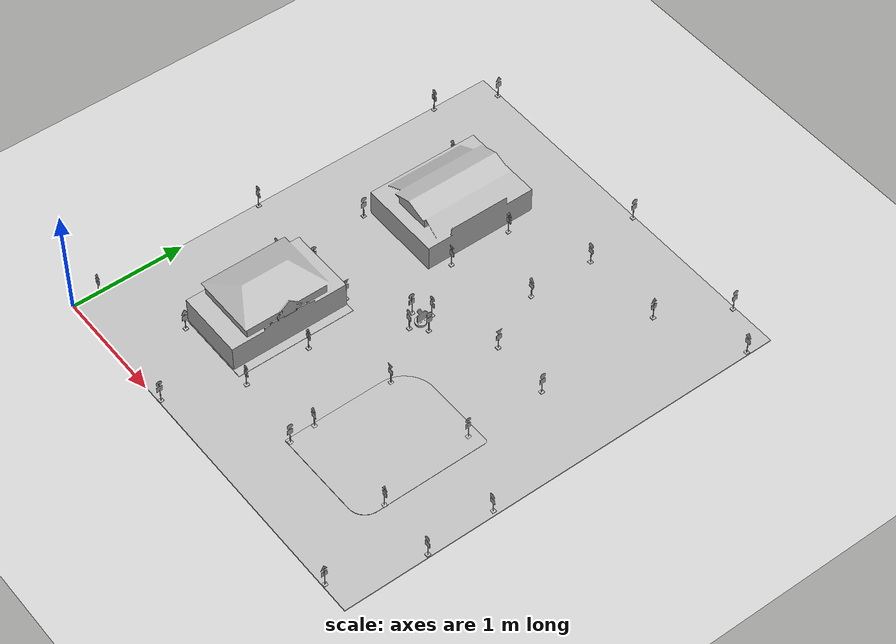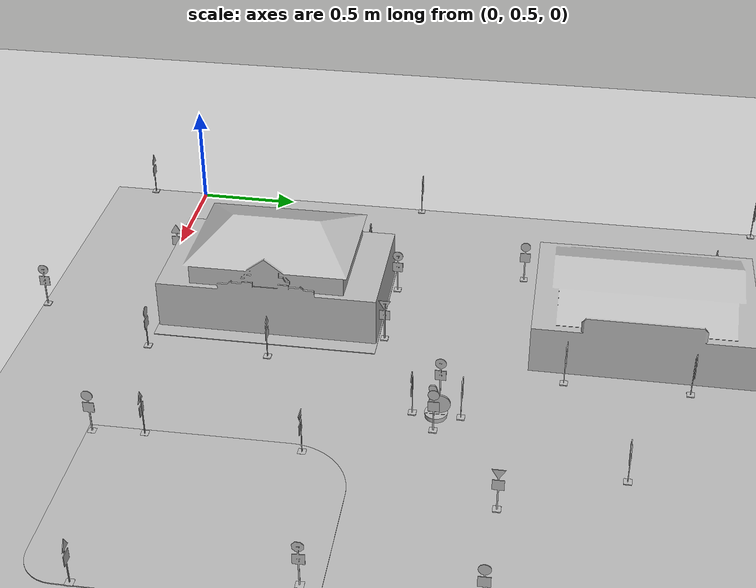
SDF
<sdf version="1.6">
 <world name="default">
  <light name="sun" type="directional">
   <pose>0 0 10 0 -0 0</pose>
   <diffuse>0.8 0.8 0.8 1</diffuse>
   <specular>0.1 0.1 0.1 1</specular>
   <attenuation>
    <range>1000</range>
    <constant>0.9</constant>
    <linear>0.01</linear>
    <quadratic>0.001</quadratic>
   </attenuation>
   <direction>-0.5 0.5 -1</direction>
  </light>
  <model name="ground_plane">
   <static>1</static>
   <link name="link">
    <collision name="collision">
     <geometry><plane><normal>0 0 1</normal><size>100 100</size></plane></geometry>
     <surface><friction><ode><mu>100</mu><mu2>50</mu2></ode></friction></surface>
    </collision>
    <visual name="visual">
     <cast_shadows>0</cast_shadows>
     <geometry><plane><normal>0 0 1</normal><size>100 100</size></plane></geometry>
     <material>
      <script><uri>file://media/materials/scripts/gazebo.material</uri><name>Gazebo/Grey</name></script>
     </material>
    </visual>
   </link>
  </model>
  <gravity>0 0 -9.8</gravity>
  <magnetic_field>6e-06 2.3e-05 -4.2e-05</magnetic_field>
  <atmosphere type="adiabatic"/>
  <physics name="default_physics" default="0" type="ode">
   <max_step_size>0.001</max_step_size>
   <real_time_factor>1</real_time_factor>
   <real_time_update_rate>1000</real_time_update_rate>
  </physics>
  <scene><ambient>0.4 0.4 0.4 1</ambient><background>0.7 0.7 0.7 1</background><shadows>1</shadows></scene>
  <spherical_coordinates>
   <surface_model>EARTH_WGS84</surface_model>
   <latitude_deg>0</latitude_deg>
   <longitude_deg>0</longitude_deg>
   <elevation>0</elevation>
   <heading_deg>0</heading_deg>
  </spherical_coordinates>
  <model name="bigcity">
   <pose>0 0 0.002788 0 -0 0</pose>
   <link name="link_0">
    <inertial>
     <mass>1</mass>
     <inertia>
      <ixx>0.166667</ixx>
      <ixy>0</ixy>
      <ixz>0</ixz>
      <iyy>0.166667</iyy>
      <iyz>0</iyz>
      <izz>0.166667</izz>
     </inertia>
    </inertial>
    <visual name="visual">
     <geometry><mesh><uri>file://models/stl/daeBlender/bigcity.dae</uri><scale>1 1 1</scale></mesh></geometry>
     <material><shader type="pixel"><normal_map>__default__</normal_map></shader></material>
    </visual>
    <collision name="collision">
     <pose>1.75 2 -0.03 0 -0 0</pose>
     <geometry><box><size>3.6 4.1 0.08</size></box></geometry>
     <surface>
      <friction>
       <ode><mu>1</mu><mu2>1</mu2><fdir1>0 0 0</fdir1><slip1>0</slip1><slip2>0</slip2></ode>
       <torsional>
        <coefficient>1</coefficient>
        <patch_radius>0</patch_radius>
        <surface_radius>0</surface_radius>
        <use_patch_radius>1</use_patch_radius>
        <ode><slip>0</slip></ode>
       </torsional>
      </friction>
      <bounce><restitution_coefficient>0</restitution_coefficient><threshold>1e+06</threshold></bounce>
      <contact>
       <collide_without_contact>0</collide_without_contact>
       <collide_without_contact_bitmask>1</collide_without_contact_bitmask>
       <collide_bitmask>1</collide_bitmask>
       <ode>
        <soft_cfm>0</soft_cfm>
        <soft_erp>0.2</soft_erp>
        <kp>1e+13</kp>
        <kd>1</kd>
        <max_vel>0.01</max_vel>
        <min_depth>0</min_depth>
       </ode>
       <bullet>
        <split_impulse>1</split_impulse>
        <split_impulse_penetration_threshold>-0.01</split_impulse_penetration_threshold>
        <soft_cfm>0</soft_cfm>
        <soft_erp>0.2</soft_erp>
        <kp>1e+13</kp>
        <kd>1</kd>
       </bullet>
      </contact>
     </surface>
    </collision>
   </link>
   <static>1</static>
  </model>
  <model name="peatones_qr">
   <link name="link_6">
    <inertial>
     <mass>0.02</mass>
     <inertia>
      <ixx>0.166667</ixx>
      <ixy>0</ixy>
      <ixz>0</ixz>
      <iyy>0.166667</iyy>
      <iyz>0</iyz>
      <izz>0.166667</izz>
     </inertia>
    </inertial>
    <visual name="visual">
     <geometry>
      <mesh><uri>file://models/stl/SENALES_QR/PEATONES/peatones_qr.dae</uri><scale>1 1 1</scale></mesh>
     </geometry>
    </visual>
    <collision name="collision">
     <geometry>
      <mesh><uri>file://models/stl/SENALES_QR/PEATONES/peatones_qr.dae</uri><scale>1 1 1</scale></mesh>
     </geometry>
     <surface>
      <friction>
       <ode><mu>1</mu><mu2>1</mu2><fdir1>0 0 0</fdir1><slip1>0</slip1><slip2>0</slip2></ode>
       <torsional>
        <coefficient>1</coefficient>
        <patch_radius>0</patch_radius>
        <surface_radius>0</surface_radius>
        <use_patch_radius>1</use_patch_radius>
        <ode><slip>0</slip></ode>
       </torsional>
      </friction>
      <bounce><restitution_coefficient>0</restitution_coefficient><threshold>1e+06</threshold></bounce>
      <contact>
       <collide_without_contact>0</collide_without_contact>
       <collide_without_contact_bitmask>1</collide_without_contact_bitmask>
       <collide_bitmask>1</collide_bitmask>
       <ode>
        <soft_cfm>0</soft_cfm>
        <soft_erp>0.2</soft_erp>
        <kp>1e+13</kp>
        <kd>1</kd>
        <max_vel>0.01</max_vel>
        <min_depth>0</min_depth>
       </ode>
       <bullet>
        <split_impulse>1</split_impulse>
        <split_impulse_penetration_threshold>-0.01</split_impulse_penetration_threshold>
        <soft_cfm>0</soft_cfm>
        <soft_erp>0.2</soft_erp>
        <kp>1e+13</kp>
        <kd>1</kd>
       </bullet>
      </contact>
     </surface>
    </collision>
   </link>
   <static>0</static>
   <pose>2.06366 0.780848 0.012778 3e-06 -4e-06 0</pose>
  </model>
  <model name="parar_qr">
   <link name="link_4">
    <inertial>
     <mass>0.02</mass>
     <inertia>
      <ixx>0.166667</ixx>
      <ixy>0</ixy>
      <ixz>0</ixz>
      <iyy>0.166667</iyy>
      <iyz>0</iyz>
      <izz>0.166667</izz>
     </inertia>
    </inertial>
    <visual name="visual">
     <geometry>
      <mesh><uri>file://models/stl/SENALES_QR/PARAR/parar_qr.dae</uri><scale>1 1 1</scale></mesh>
     </geometry>
    </visual>
    <collision name="collision">
     <geometry>
      <mesh><uri>file://models/stl/SENALES_QR/PARAR/parar_qr.dae</uri><scale>1 1 1</scale></mesh>
     </geometry>
     <surface>
      <friction>
       <ode><mu>1</mu><mu2>1</mu2><fdir1>0 0 0</fdir1><slip1>0</slip1><slip2>0</slip2></ode>
       <torsional>
        <coefficient>1</coefficient>
        <patch_radius>0</patch_radius>
        <surface_radius>0</surface_radius>
        <use_patch_radius>1</use_patch_radius>
        <ode><slip>0</slip></ode>
       </torsional>
      </friction>
      <bounce><restitution_coefficient>0</restitution_coefficient><threshold>1e+06</threshold></bounce>
      <contact>
       <collide_without_contact>0</collide_without_contact>
       <collide_without_contact_bitmask>1</collide_without_contact_bitmask>
       <collide_bitmask>1</collide_bitmask>
       <ode>
        <soft_cfm>0</soft_cfm>
        <soft_erp>0.2</soft_erp>
        <kp>1e+13</kp>
        <kd>1</kd>
        <max_vel>0.01</max_vel>
        <min_depth>0</min_depth>
       </ode>
       <bullet>
        <split_impulse>1</split_impulse>
        <split_impulse_penetration_threshold>-0.01</split_impulse_penetration_threshold>
        <soft_cfm>0</soft_cfm>
        <soft_erp>0.2</soft_erp>
        <kp>1e+13</kp>
        <kd>1</kd>
       </bullet>
      </contact>
     </surface>
    </collision>
   </link>
   <static>0</static>
   <pose>2.06988 3.41979 0.012778 0 -2e-06 0</pose>
  </model>
  <model name="rotonda_qr">
   <link name="link_9">
    <inertial>
     <mass>0.02</mass>
     <inertia>
      <ixx>0.166667</ixx>
      <ixy>0</ixy>
      <ixz>0</ixz>
      <iyy>0.166667</iyy>
      <iyz>0</iyz>
      <izz>0.166667</izz>
     </inertia>
    </inertial>
    <visual name="visual">
     <geometry>
      <mesh><uri>file://models/stl/SENALES_QR/ROTONDA/rotonda_qr.dae</uri><scale>1 1 1</scale></mesh>
     </geometry>
    </visual>
    <collision name="collision">
     <geometry>
      <mesh><uri>file://models/stl/SENALES_QR/ROTONDA/rotonda_qr.dae</uri><scale>1 1 1</scale></mesh>
     </geometry>
     <surface>
      <friction>
       <ode><mu>1</mu><mu2>1</mu2><fdir1>0 0 0</fdir1><slip1>0</slip1><slip2>0</slip2></ode>
       <torsional>
        <coefficient>1</coefficient>
        <patch_radius>0</patch_radius>
        <surface_radius>0</surface_radius>
        <use_patch_radius>1</use_patch_radius>
        <ode><slip>0</slip></ode>
       </torsional>
      </friction>
      <bounce><restitution_coefficient>0</restitution_coefficient><threshold>1e+06</threshold></bounce>
      <contact>
       <collide_without_contact>0</collide_without_contact>
       <collide_without_contact_bitmask>1</collide_without_contact_bitmask>
       <collide_bitmask>1</collide_bitmask>
       <ode>
        <soft_cfm>0</soft_cfm>
        <soft_erp>0.2</soft_erp>
        <kp>1e+13</kp>
        <kd>1</kd>
        <max_vel>0.01</max_vel>
        <min_depth>0</min_depth>
       </ode>
       <bullet>
        <split_impulse>1</split_impulse>
        <split_impulse_penetration_threshold>-0.01</split_impulse_penetration_threshold>
        <soft_cfm>0</soft_cfm>
        <soft_erp>0.2</soft_erp>
        <kp>1e+13</kp>
        <kd>1</kd>
       </bullet>
      </contact>
     </surface>
    </collision>
   </link>
   <static>0</static>
   <pose>1.74923 1.89715 0.012778 5e-06 -0 -0.006442</pose>
  </model>
  <model name="ceda_qr">
   <link name="link_0">
    <inertial>
     <mass>0.02</mass>
     <inertia>
      <ixx>0.166667</ixx>
      <ixy>0</ixy>
      <ixz>0</ixz>
      <iyy>0.166667</iyy>
      <iyz>0</iyz>
      <izz>0.166667</izz>
     </inertia>
    </inertial>
    <visual name="visual">
     <geometry><mesh><uri>file://models/stl/SENALES_QR/CEDA/ceda_qr.dae</uri><scale>1 1 1</scale></mesh></geometry>
    </visual>
    <collision name="collision">
     <geometry><mesh><uri>file://models/stl/SENALES_QR/CEDA/ceda_qr.dae</uri><scale>1 1 1</scale></mesh></geometry>
     <surface>
      <friction>
       <ode><mu>1</mu><mu2>1</mu2><fdir1>0 0 0</fdir1><slip1>0</slip1><slip2>0</slip2></ode>
       <torsional>
        <coefficient>1</coefficient>
        <patch_radius>0</patch_radius>
        <surface_radius>0</surface_radius>
        <use_patch_radius>1</use_patch_radius>
        <ode><slip>0</slip></ode>
       </torsional>
      </friction>
      <bounce><restitution_coefficient>0</restitution_coefficient><threshold>1e+06</threshold></bounce>
      <contact>
       <collide_without_contact>0</collide_without_contact>
       <collide_without_contact_bitmask>1</collide_without_contact_bitmask>
       <collide_bitmask>1</collide_bitmask>
       <ode>
        <soft_cfm>0</soft_cfm>
        <soft_erp>0.2</soft_erp>
        <kp>1e+13</kp>
        <kd>1</kd>
        <max_vel>0.01</max_vel>
        <min_depth>0</min_depth>
       </ode>
       <bullet>
        <split_impulse>1</split_impulse>
        <split_impulse_penetration_threshold>-0.01</split_impulse_penetration_threshold>
        <soft_cfm>0</soft_cfm>
        <soft_erp>0.2</soft_erp>
        <kp>1e+13</kp>
        <kd>1</kd>
       </bullet>
      </contact>
     </surface>
    </collision>
   </link>
   <static>0</static>
   <pose>2.08023 1.47221 0.012778 1e-06 -1e-06 0</pose>
  </model>
  <model name="velocidad50_qr">
   <link name="link_14">
    <inertial>
     <mass>0.02</mass>
     <inertia>
      <ixx>0.166667</ixx>
      <ixy>0</ixy>
      <ixz>0</ixz>
      <iyy>0.166667</iyy>
      <iyz>0</iyz>
      <izz>0.166667</izz>
     </inertia>
    </inertial>
    <visual name="visual">
     <geometry>
      <mesh><uri>file://models/stl/SENALES_QR/VELOCIDAD50/velo50_qr.dae</uri><scale>1 1 1</scale></mesh>
     </geometry>
    </visual>
    <collision name="collision">
     <geometry>
      <mesh><uri>file://models/stl/SENALES_QR/VELOCIDAD50/velo50_qr.dae</uri><scale>1 1 1</scale></mesh>
     </geometry>
     <surface>
      <friction>
       <ode><mu>1</mu><mu2>1</mu2><fdir1>0 0 0</fdir1><slip1>0</slip1><slip2>0</slip2></ode>
       <torsional>
        <coefficient>1</coefficient>
        <patch_radius>0</patch_radius>
        <surface_radius>0</surface_radius>
        <use_patch_radius>1</use_patch_radius>
        <ode><slip>0</slip></ode>
       </torsional>
      </friction>
      <bounce><restitution_coefficient>0</restitution_coefficient><threshold>1e+06</threshold></bounce>
      <contact>
       <collide_without_contact>0</collide_without_contact>
       <collide_without_contact_bitmask>1</collide_without_contact_bitmask>
       <collide_bitmask>1</collide_bitmask>
       <ode>
        <soft_cfm>0</soft_cfm>
        <soft_erp>0.2</soft_erp>
        <kp>1e+13</kp>
        <kd>1</kd>
        <max_vel>0.01</max_vel>
        <min_depth>0</min_depth>
       </ode>
       <bullet>
        <split_impulse>1</split_impulse>
        <split_impulse_penetration_threshold>-0.01</split_impulse_penetration_threshold>
        <soft_cfm>0</soft_cfm>
        <soft_erp>0.2</soft_erp>
        <kp>1e+13</kp>
        <kd>1</kd>
       </bullet>
      </contact>
     </surface>
    </collision>
   </link>
   <static>0</static>
   <pose>0.020585 3.47057 0.012793 -1.3e-05 -0.000245 -3.13702</pose>
  </model>
  <model name="velocidad20_qr_0">
   <link name="link_12">
    <inertial>
     <mass>0.02</mass>
     <inertia>
      <ixx>0.166667</ixx>
      <ixy>0</ixy>
      <ixz>0</ixz>
      <iyy>0.166667</iyy>
      <iyz>0</iyz>
      <izz>0.166667</izz>
     </inertia>
    </inertial>
    <visual name="visual">
     <geometry>
      <mesh><uri>file://models/stl/SENALES_QR/VELOCIDAD20/velo20_qr.dae</uri><scale>1 1 1</scale></mesh>
     </geometry>
    </visual>
    <collision name="collision">
     <geometry>
      <mesh><uri>file://models/stl/SENALES_QR/VELOCIDAD20/velo20_qr.dae</uri><scale>1 1 1</scale></mesh>
     </geometry>
     <surface>
      <friction>
       <ode><mu>1</mu><mu2>1</mu2><fdir1>0 0 0</fdir1><slip1>0</slip1><slip2>0</slip2></ode>
       <torsional>
        <coefficient>1</coefficient>
        <patch_radius>0</patch_radius>
        <surface_radius>0</surface_radius>
        <use_patch_radius>1</use_patch_radius>
        <ode><slip>0</slip></ode>
       </torsional>
      </friction>
      <bounce><restitution_coefficient>0</restitution_coefficient><threshold>1e+06</threshold></bounce>
      <contact>
       <collide_without_contact>0</collide_without_contact>
       <collide_without_contact_bitmask>1</collide_without_contact_bitmask>
       <collide_bitmask>1</collide_bitmask>
       <ode>
        <soft_cfm>0</soft_cfm>
        <soft_erp>0.2</soft_erp>
        <kp>1e+13</kp>
        <kd>1</kd>
        <max_vel>0.01</max_vel>
        <min_depth>0</min_depth>
       </ode>
       <bullet>
        <split_impulse>1</split_impulse>
        <split_impulse_penetration_threshold>-0.01</split_impulse_penetration_threshold>
        <soft_cfm>0</soft_cfm>
        <soft_erp>0.2</soft_erp>
        <kp>1e+13</kp>
        <kd>1</kd>
       </bullet>
      </contact>
     </surface>
    </collision>
   </link>
   <static>0</static>
   <pose>0.021141 1.71898 0.012785 -6e-06 -0.000353 -3.13232</pose>
  </model>
  <model name="peligro_izqu_qr_1">
   <link name="link_8">
    <inertial>
     <mass>0.02</mass>
     <inertia>
      <ixx>0.166667</ixx>
      <ixy>0</ixy>
      <ixz>0</ixz>
      <iyy>0.166667</iyy>
      <iyz>0</iyz>
      <izz>0.166667</izz>
     </inertia>
    </inertial>
    <visual name="visual">
     <geometry>
      <mesh><uri>file://models/stl/SENALES_QR/PELIGRO IZQUIERDA/peligr_izq_qr.dae</uri><scale>1 1 1</scale></mesh>
     </geometry>
    </visual>
    <collision name="collision">
     <geometry>
      <mesh><uri>file://models/stl/SENALES_QR/PELIGRO IZQUIERDA/peligr_izq_qr.dae</uri><scale>1 1 1</scale></mesh>
     </geometry>
     <surface>
      <friction>
       <ode><mu>1</mu><mu2>1</mu2><fdir1>0 0 0</fdir1><slip1>0</slip1><slip2>0</slip2></ode>
       <torsional>
        <coefficient>1</coefficient>
        <patch_radius>0</patch_radius>
        <surface_radius>0</surface_radius>
        <use_patch_radius>1</use_patch_radius>
        <ode><slip>0</slip></ode>
       </torsional>
      </friction>
      <bounce><restitution_coefficient>0</restitution_coefficient><threshold>1e+06</threshold></bounce>
      <contact>
       <collide_without_contact>0</collide_without_contact>
       <collide_without_contact_bitmask>1</collide_without_contact_bitmask>
       <collide_bitmask>1</collide_bitmask>
       <ode>
        <soft_cfm>0</soft_cfm>
        <soft_erp>0.2</soft_erp>
        <kp>1e+13</kp>
        <kd>1</kd>
        <max_vel>0.01</max_vel>
        <min_depth>0</min_depth>
       </ode>
       <bullet>
        <split_impulse>1</split_impulse>
        <split_impulse_penetration_threshold>-0.01</split_impulse_penetration_threshold>
        <soft_cfm>0</soft_cfm>
        <soft_erp>0.2</soft_erp>
        <kp>1e+13</kp>
        <kd>1</kd>
       </bullet>
      </contact>
     </surface>
    </collision>
   </link>
   <static>0</static>
   <pose>2.94773 0.762295 0.012852 0.003496 -0.000526 3.14111</pose>
  </model>
  <model name="peatones_qr_0">
   <link name="link_6">
    <inertial>
     <mass>0.02</mass>
     <inertia>
      <ixx>0.166667</ixx>
      <ixy>0</ixy>
      <ixz>0</ixz>
      <iyy>0.166667</iyy>
      <iyz>0</iyz>
      <izz>0.166667</izz>
     </inertia>
    </inertial>
    <visual name="visual">
     <geometry>
      <mesh><uri>file://models/stl/SENALES_QR/PEATONES/peatones_qr.dae</uri><scale>1 1 1</scale></mesh>
     </geometry>
    </visual>
    <collision name="collision">
     <geometry>
      <mesh><uri>file://models/stl/SENALES_QR/PEATONES/peatones_qr.dae</uri><scale>1 1 1</scale></mesh>
     </geometry>
     <surface>
      <friction>
       <ode><mu>1</mu><mu2>1</mu2><fdir1>0 0 0</fdir1><slip1>0</slip1><slip2>0</slip2></ode>
       <torsional>
        <coefficient>1</coefficient>
        <patch_radius>0</patch_radius>
        <surface_radius>0</surface_radius>
        <use_patch_radius>1</use_patch_radius>
        <ode><slip>0</slip></ode>
       </torsional>
      </friction>
      <bounce><restitution_coefficient>0</restitution_coefficient><threshold>1e+06</threshold></bounce>
      <contact>
       <collide_without_contact>0</collide_without_contact>
       <collide_without_contact_bitmask>1</collide_without_contact_bitmask>
       <collide_bitmask>1</collide_bitmask>
       <ode>
        <soft_cfm>0</soft_cfm>
        <soft_erp>0.2</soft_erp>
        <kp>1e+13</kp>
        <kd>1</kd>
        <max_vel>0.01</max_vel>
        <min_depth>0</min_depth>
       </ode>
       <bullet>
        <split_impulse>1</split_impulse>
        <split_impulse_penetration_threshold>-0.01</split_impulse_penetration_threshold>
        <soft_cfm>0</soft_cfm>
        <soft_erp>0.2</soft_erp>
        <kp>1e+13</kp>
        <kd>1</kd>
       </bullet>
      </contact>
     </surface>
    </collision>
   </link>
   <static>0</static>
   <pose>1.4378 3.11152 0.012852 0.001017 -0.00282 3.13618</pose>
  </model>
  <model name="peatones_qr_1">
   <link name="link_6">
    <inertial>
     <mass>0.02</mass>
     <inertia>
      <ixx>0.166667</ixx>
      <ixy>0</ixy>
      <ixz>0</ixz>
      <iyy>0.166667</iyy>
      <iyz>0</iyz>
      <izz>0.166667</izz>
     </inertia>
    </inertial>
    <visual name="visual">
     <geometry>
      <mesh><uri>file://models/stl/SENALES_QR/PEATONES/peatones_qr.dae</uri><scale>1 1 1</scale></mesh>
     </geometry>
    </visual>
    <collision name="collision">
     <geometry>
      <mesh><uri>file://models/stl/SENALES_QR/PEATONES/peatones_qr.dae</uri><scale>1 1 1</scale></mesh>
     </geometry>
     <surface>
      <friction>
       <ode><mu>1</mu><mu2>1</mu2><fdir1>0 0 0</fdir1><slip1>0</slip1><slip2>0</slip2></ode>
       <torsional>
        <coefficient>1</coefficient>
        <patch_radius>0</patch_radius>
        <surface_radius>0</surface_radius>
        <use_patch_radius>1</use_patch_radius>
        <ode><slip>0</slip></ode>
       </torsional>
      </friction>
      <bounce><restitution_coefficient>0</restitution_coefficient><threshold>1e+06</threshold></bounce>
      <contact>
       <collide_without_contact>0</collide_without_contact>
       <collide_without_contact_bitmask>1</collide_without_contact_bitmask>
       <collide_bitmask>1</collide_bitmask>
       <ode>
        <soft_cfm>0</soft_cfm>
        <soft_erp>0.2</soft_erp>
        <kp>1e+13</kp>
        <kd>1</kd>
        <max_vel>0.01</max_vel>
        <min_depth>0</min_depth>
       </ode>
       <bullet>
        <split_impulse>1</split_impulse>
        <split_impulse_penetration_threshold>-0.01</split_impulse_penetration_threshold>
        <soft_cfm>0</soft_cfm>
        <soft_erp>0.2</soft_erp>
        <kp>1e+13</kp>
        <kd>1</kd>
       </bullet>
      </contact>
     </surface>
    </collision>
   </link>
   <static>0</static>
   <pose>1.44096 1.18121 0.012847 -0.000252 0.003176 3.12914</pose>
  </model>
  <model name="parar_qr_0">
   <link name="link_4">
    <inertial>
     <mass>0.02</mass>
     <inertia>
      <ixx>0.166667</ixx>
      <ixy>0</ixy>
      <ixz>0</ixz>
      <iyy>0.166667</iyy>
      <iyz>0</iyz>
      <izz>0.166667</izz>
     </inertia>
    </inertial>
    <visual name="visual">
     <geometry>
      <mesh><uri>file://models/stl/SENALES_QR/PARAR/parar_qr.dae</uri><scale>1 1 1</scale></mesh>
     </geometry>
    </visual>
    <collision name="collision">
     <geometry>
      <mesh><uri>file://models/stl/SENALES_QR/PARAR/parar_qr.dae</uri><scale>1 1 1</scale></mesh>
     </geometry>
     <surface>
      <friction>
       <ode><mu>1</mu><mu2>1</mu2><fdir1>0 0 0</fdir1><slip1>0</slip1><slip2>0</slip2></ode>
       <torsional>
        <coefficient>1</coefficient>
        <patch_radius>0</patch_radius>
        <surface_radius>0</surface_radius>
        <use_patch_radius>1</use_patch_radius>
        <ode><slip>0</slip></ode>
       </torsional>
      </friction>
      <bounce><restitution_coefficient>0</restitution_coefficient><threshold>1e+06</threshold></bounce>
      <contact>
       <collide_without_contact>0</collide_without_contact>
       <collide_without_contact_bitmask>1</collide_without_contact_bitmask>
       <collide_bitmask>1</collide_bitmask>
       <ode>
        <soft_cfm>0</soft_cfm>
        <soft_erp>0.2</soft_erp>
        <kp>1e+13</kp>
        <kd>1</kd>
        <max_vel>0.01</max_vel>
        <min_depth>0</min_depth>
       </ode>
       <bullet>
        <split_impulse>1</split_impulse>
        <split_impulse_penetration_threshold>-0.01</split_impulse_penetration_threshold>
        <soft_cfm>0</soft_cfm>
        <soft_erp>0.2</soft_erp>
        <kp>1e+13</kp>
        <kd>1</kd>
       </bullet>
      </contact>
     </surface>
    </collision>
   </link>
   <static>0</static>
   <pose>1.4427 0.609211 0.012789 5.9e-05 -1.1e-05 3.12888</pose>
  </model>
  <model name="ceda_qr_0">
   <link name="link_0">
    <inertial>
     <mass>0.02</mass>
     <inertia>
      <ixx>0.166667</ixx>
      <ixy>0</ixy>
      <ixz>0</ixz>
      <iyy>0.166667</iyy>
      <iyz>0</iyz>
      <izz>0.166667</izz>
     </inertia>
    </inertial>
    <visual name="visual">
     <geometry><mesh><uri>file://models/stl/SENALES_QR/CEDA/ceda_qr.dae</uri><scale>1 1 1</scale></mesh></geometry>
    </visual>
    <collision name="collision">
     <geometry><mesh><uri>file://models/stl/SENALES_QR/CEDA/ceda_qr.dae</uri><scale>1 1 1</scale></mesh></geometry>
     <surface>
      <friction>
       <ode><mu>1</mu><mu2>1</mu2><fdir1>0 0 0</fdir1><slip1>0</slip1><slip2>0</slip2></ode>
       <torsional>
        <coefficient>1</coefficient>
        <patch_radius>0</patch_radius>
        <surface_radius>0</surface_radius>
        <use_patch_radius>1</use_patch_radius>
        <ode><slip>0</slip></ode>
       </torsional>
      </friction>
      <bounce><restitution_coefficient>0</restitution_coefficient><threshold>1e+06</threshold></bounce>
      <contact>
       <collide_without_contact>0</collide_without_contact>
       <collide_without_contact_bitmask>1</collide_without_contact_bitmask>
       <collide_bitmask>1</collide_bitmask>
       <ode>
        <soft_cfm>0</soft_cfm>
        <soft_erp>0.2</soft_erp>
        <kp>1e+13</kp>
        <kd>1</kd>
        <max_vel>0.01</max_vel>
        <min_depth>0</min_depth>
       </ode>
       <bullet>
        <split_impulse>1</split_impulse>
        <split_impulse_penetration_threshold>-0.01</split_impulse_penetration_threshold>
        <soft_cfm>0</soft_cfm>
        <soft_erp>0.2</soft_erp>
        <kp>1e+13</kp>
        <kd>1</kd>
       </bullet>
      </contact>
     </surface>
    </collision>
   </link>
   <static>0</static>
   <pose>1.43736 2.54785 0.012779 7e-06 -9e-06 3.13292</pose>
  </model>
  <model name="peligro_drcha_qr">
   <link name="link_7">
    <inertial>
     <mass>0.02</mass>
     <inertia>
      <ixx>0.166667</ixx>
      <ixy>0</ixy>
      <ixz>0</ixz>
      <iyy>0.166667</iyy>
      <iyz>0</iyz>
      <izz>0.166667</izz>
     </inertia>
    </inertial>
    <visual name="visual">
     <geometry>
      <mesh><uri>file://models/stl/SENALES_QR/PELIGRO DERECHA/pelgr_dcha_qr.dae</uri><scale>1 1 1</scale></mesh>
     </geometry>
    </visual>
    <collision name="collision">
     <geometry>
      <mesh><uri>file://models/stl/SENALES_QR/PELIGRO DERECHA/pelgr_dcha_qr.dae</uri><scale>1 1 1</scale></mesh>
     </geometry>
     <surface>
      <friction>
       <ode><mu>1</mu><mu2>1</mu2><fdir1>0 0 0</fdir1><slip1>0</slip1><slip2>0</slip2></ode>
       <torsional>
        <coefficient>1</coefficient>
        <patch_radius>0</patch_radius>
        <surface_radius>0</surface_radius>
        <use_patch_radius>1</use_patch_radius>
        <ode><slip>0</slip></ode>
       </torsional>
      </friction>
      <bounce><restitution_coefficient>0</restitution_coefficient><threshold>1e+06</threshold></bounce>
      <contact>
       <collide_without_contact>0</collide_without_contact>
       <collide_without_contact_bitmask>1</collide_without_contact_bitmask>
       <collide_bitmask>1</collide_bitmask>
       <ode>
        <soft_cfm>0</soft_cfm>
        <soft_erp>0.2</soft_erp>
        <kp>1e+13</kp>
        <kd>1</kd>
        <max_vel>0.01</max_vel>
        <min_depth>0</min_depth>
       </ode>
       <bullet>
        <split_impulse>1</split_impulse>
        <split_impulse_penetration_threshold>-0.01</split_impulse_penetration_threshold>
        <soft_cfm>0</soft_cfm>
        <soft_erp>0.2</soft_erp>
        <kp>1e+13</kp>
        <kd>1</kd>
       </bullet>
      </contact>
     </surface>
    </collision>
   </link>
   <static>0</static>
   <pose>0.218554 3.97999 0.012889 0.001744 -0.004375 1.60988</pose>
  </model>
  <model name="peligro_drcha_qr_0">
   <link name="link_7">
    <inertial>
     <mass>0.02</mass>
     <inertia>
      <ixx>0.166667</ixx>
      <ixy>0</ixy>
      <ixz>0</ixz>
      <iyy>0.166667</iyy>
      <iyz>0</iyz>
      <izz>0.166667</izz>
     </inertia>
    </inertial>
    <visual name="visual">
     <geometry>
      <mesh><uri>file://models/stl/SENALES_QR/PELIGRO DERECHA/pelgr_dcha_qr.dae</uri><scale>1 1 1</scale></mesh>
     </geometry>
    </visual>
    <collision name="collision">
     <geometry>
      <mesh><uri>file://models/stl/SENALES_QR/PELIGRO DERECHA/pelgr_dcha_qr.dae</uri><scale>1 1 1</scale></mesh>
     </geometry>
     <surface>
      <friction>
       <ode><mu>1</mu><mu2>1</mu2><fdir1>0 0 0</fdir1><slip1>0</slip1><slip2>0</slip2></ode>
       <torsional>
        <coefficient>1</coefficient>
        <patch_radius>0</patch_radius>
        <surface_radius>0</surface_radius>
        <use_patch_radius>1</use_patch_radius>
        <ode><slip>0</slip></ode>
       </torsional>
      </friction>
      <bounce><restitution_coefficient>0</restitution_coefficient><threshold>1e+06</threshold></bounce>
      <contact>
       <collide_without_contact>0</collide_without_contact>
       <collide_without_contact_bitmask>1</collide_without_contact_bitmask>
       <collide_bitmask>1</collide_bitmask>
       <ode>
        <soft_cfm>0</soft_cfm>
        <soft_erp>0.2</soft_erp>
        <kp>1e+13</kp>
        <kd>1</kd>
        <max_vel>0.01</max_vel>
        <min_depth>0</min_depth>
       </ode>
       <bullet>
        <split_impulse>1</split_impulse>
        <split_impulse_penetration_threshold>-0.01</split_impulse_penetration_threshold>
        <soft_cfm>0</soft_cfm>
        <soft_erp>0.2</soft_erp>
        <kp>1e+13</kp>
        <kd>1</kd>
       </bullet>
      </contact>
     </surface>
    </collision>
   </link>
   <static>0</static>
   <pose>0.020053 0.222677 0.012778 -2e-06 -2e-06 -3.12939</pose>
  </model>
  <model name="velocidad20_qr_1">
   <link name="link_12">
    <inertial>
     <mass>0.02</mass>
     <inertia>
      <ixx>0.166667</ixx>
      <ixy>0</ixy>
      <ixz>0</ixz>
      <iyy>0.166667</iyy>
      <iyz>0</iyz>
      <izz>0.166667</izz>
     </inertia>
    </inertial>
    <visual name="visual">
     <geometry>
      <mesh><uri>file://models/stl/SENALES_QR/VELOCIDAD20/velo20_qr.dae</uri><scale>1 1 1</scale></mesh>
     </geometry>
    </visual>
    <collision name="collision">
     <geometry>
      <mesh><uri>file://models/stl/SENALES_QR/VELOCIDAD20/velo20_qr.dae</uri><scale>1 1 1</scale></mesh>
     </geometry>
     <surface>
      <friction>
       <ode><mu>1</mu><mu2>1</mu2><fdir1>0 0 0</fdir1><slip1>0</slip1><slip2>0</slip2></ode>
       <torsional>
        <coefficient>1</coefficient>
        <patch_radius>0</patch_radius>
        <surface_radius>0</surface_radius>
        <use_patch_radius>1</use_patch_radius>
        <ode><slip>0</slip></ode>
       </torsional>
      </friction>
      <bounce><restitution_coefficient>0</restitution_coefficient><threshold>1e+06</threshold></bounce>
      <contact>
       <collide_without_contact>0</collide_without_contact>
       <collide_without_contact_bitmask>1</collide_without_contact_bitmask>
       <collide_bitmask>1</collide_bitmask>
       <ode>
        <soft_cfm>0</soft_cfm>
        <soft_erp>0.2</soft_erp>
        <kp>1e+13</kp>
        <kd>1</kd>
        <max_vel>0.01</max_vel>
        <min_depth>0</min_depth>
       </ode>
       <bullet>
        <split_impulse>1</split_impulse>
        <split_impulse_penetration_threshold>-0.01</split_impulse_penetration_threshold>
        <soft_cfm>0</soft_cfm>
        <soft_erp>0.2</soft_erp>
        <kp>1e+13</kp>
        <kd>1</kd>
       </bullet>
      </contact>
     </surface>
    </collision>
   </link>
   <static>0</static>
   <pose>0.79834 1.69678 0.012778 -2e-06 -0 -1.59311</pose>
  </model>
  <model name="ceda_qr_1">
   <link name="link_0">
    <inertial>
     <mass>0.02</mass>
     <inertia>
      <ixx>0.166667</ixx>
      <ixy>0</ixy>
      <ixz>0</ixz>
      <iyy>0.166667</iyy>
      <iyz>0</iyz>
      <izz>0.166667</izz>
     </inertia>
    </inertial>
    <visual name="visual">
     <geometry><mesh><uri>file://models/stl/SENALES_QR/CEDA/ceda_qr.dae</uri><scale>1 1 1</scale></mesh></geometry>
    </visual>
    <collision name="collision">
     <geometry><mesh><uri>file://models/stl/SENALES_QR/CEDA/ceda_qr.dae</uri><scale>1 1 1</scale></mesh></geometry>
     <surface>
      <friction>
       <ode><mu>1</mu><mu2>1</mu2><fdir1>0 0 0</fdir1><slip1>0</slip1><slip2>0</slip2></ode>
       <torsional>
        <coefficient>1</coefficient>
        <patch_radius>0</patch_radius>
        <surface_radius>0</surface_radius>
        <use_patch_radius>1</use_patch_radius>
        <ode><slip>0</slip></ode>
       </torsional>
      </friction>
      <bounce><restitution_coefficient>0</restitution_coefficient><threshold>1e+06</threshold></bounce>
      <contact>
       <collide_without_contact>0</collide_without_contact>
       <collide_without_contact_bitmask>1</collide_without_contact_bitmask>
       <collide_bitmask>1</collide_bitmask>
       <ode>
        <soft_cfm>0</soft_cfm>
        <soft_erp>0.2</soft_erp>
        <kp>1e+13</kp>
        <kd>1</kd>
        <max_vel>0.01</max_vel>
        <min_depth>0</min_depth>
       </ode>
       <bullet>
        <split_impulse>1</split_impulse>
        <split_impulse_penetration_threshold>-0.01</split_impulse_penetration_threshold>
        <soft_cfm>0</soft_cfm>
        <soft_erp>0.2</soft_erp>
        <kp>1e+13</kp>
        <kd>1</kd>
       </bullet>
      </contact>
     </surface>
    </collision>
   </link>
   <static>0</static>
   <pose>1.2171 1.69453 0.012778 -2e-06 -5e-06 -1.57502</pose>
  </model>
  <model name="velocidad40_qr_0">
   <link name="link_13">
    <inertial>
     <mass>0.02</mass>
     <inertia>
      <ixx>0.166667</ixx>
      <ixy>0</ixy>
      <ixz>0</ixz>
      <iyy>0.166667</iyy>
      <iyz>0</iyz>
      <izz>0.166667</izz>
     </inertia>
    </inertial>
    <visual name="visual">
     <geometry>
      <mesh><uri>file://models/stl/SENALES_QR/VELOCIDAD40/velo40_qr.dae</uri><scale>1 1 1</scale></mesh>
     </geometry>
    </visual>
    <collision name="collision">
     <geometry>
      <mesh><uri>file://models/stl/SENALES_QR/VELOCIDAD40/velo40_qr.dae</uri><scale>1 1 1</scale></mesh>
     </geometry>
     <surface>
      <friction>
       <ode><mu>1</mu><mu2>1</mu2><fdir1>0 0 0</fdir1><slip1>0</slip1><slip2>0</slip2></ode>
       <torsional>
        <coefficient>1</coefficient>
        <patch_radius>0</patch_radius>
        <surface_radius>0</surface_radius>
        <use_patch_radius>1</use_patch_radius>
        <ode><slip>0</slip></ode>
       </torsional>
      </friction>
      <bounce><restitution_coefficient>0</restitution_coefficient><threshold>1e+06</threshold></bounce>
      <contact>
       <collide_without_contact>0</collide_without_contact>
       <collide_without_contact_bitmask>1</collide_without_contact_bitmask>
       <collide_bitmask>1</collide_bitmask>
       <ode>
        <soft_cfm>0</soft_cfm>
        <soft_erp>0.2</soft_erp>
        <kp>1e+13</kp>
        <kd>1</kd>
        <max_vel>0.01</max_vel>
        <min_depth>0</min_depth>
       </ode>
       <bullet>
        <split_impulse>1</split_impulse>
        <split_impulse_penetration_threshold>-0.01</split_impulse_penetration_threshold>
        <soft_cfm>0</soft_cfm>
        <soft_erp>0.2</soft_erp>
        <kp>1e+13</kp>
        <kd>1</kd>
       </bullet>
      </contact>
     </surface>
    </collision>
   </link>
   <static>0</static>
   <pose>1.17735 0.019072 0.012811 0.002063 -3e-06 -1.5669</pose>
  </model>
  <model name="peligro_drcha_qr_1">
   <link name="link_7">
    <inertial>
     <mass>0.02</mass>
     <inertia>
      <ixx>0.166667</ixx>
      <ixy>0</ixy>
      <ixz>0</ixz>
      <iyy>0.166667</iyy>
      <iyz>0</iyz>
      <izz>0.166667</izz>
     </inertia>
    </inertial>
    <visual name="visual">
     <geometry>
      <mesh><uri>file://models/stl/SENALES_QR/PELIGRO DERECHA/pelgr_dcha_qr.dae</uri><scale>1 1 1</scale></mesh>
     </geometry>
    </visual>
    <collision name="collision">
     <geometry>
      <mesh><uri>file://models/stl/SENALES_QR/PELIGRO DERECHA/pelgr_dcha_qr.dae</uri><scale>1 1 1</scale></mesh>
     </geometry>
     <surface>
      <friction>
       <ode><mu>1</mu><mu2>1</mu2><fdir1>0 0 0</fdir1><slip1>0</slip1><slip2>0</slip2></ode>
       <torsional>
        <coefficient>1</coefficient>
        <patch_radius>0</patch_radius>
        <surface_radius>0</surface_radius>
        <use_patch_radius>1</use_patch_radius>
        <ode><slip>0</slip></ode>
       </torsional>
      </friction>
      <bounce><restitution_coefficient>0</restitution_coefficient><threshold>1e+06</threshold></bounce>
      <contact>
       <collide_without_contact>0</collide_without_contact>
       <collide_without_contact_bitmask>1</collide_without_contact_bitmask>
       <collide_bitmask>1</collide_bitmask>
       <ode>
        <soft_cfm>0</soft_cfm>
        <soft_erp>0.2</soft_erp>
        <kp>1e+13</kp>
        <kd>1</kd>
        <max_vel>0.01</max_vel>
        <min_depth>0</min_depth>
       </ode>
       <bullet>
        <split_impulse>1</split_impulse>
        <split_impulse_penetration_threshold>-0.01</split_impulse_penetration_threshold>
        <soft_cfm>0</soft_cfm>
        <soft_erp>0.2</soft_erp>
        <kp>1e+13</kp>
        <kd>1</kd>
       </bullet>
      </contact>
     </surface>
    </collision>
   </link>
   <static>0</static>
   <pose>3.23944 0.019825 0.012788 1.7e-05 -1e-06 -1.56956</pose>
  </model>
  <model name="rotonda_qr_2">
   <link name="link_9">
    <inertial>
     <mass>0.02</mass>
     <inertia>
      <ixx>0.166667</ixx>
      <ixy>0</ixy>
      <ixz>0</ixz>
      <iyy>0.166667</iyy>
      <iyz>0</iyz>
      <izz>0.166667</izz>
     </inertia>
    </inertial>
    <visual name="visual">
     <geometry>
      <mesh><uri>file://models/stl/SENALES_QR/ROTONDA/rotonda_qr.dae</uri><scale>1 1 1</scale></mesh>
     </geometry>
    </visual>
    <collision name="collision">
     <geometry>
      <mesh><uri>file://models/stl/SENALES_QR/ROTONDA/rotonda_qr.dae</uri><scale>1 1 1</scale></mesh>
     </geometry>
     <surface>
      <friction>
       <ode><mu>1</mu><mu2>1</mu2><fdir1>0 0 0</fdir1><slip1>0</slip1><slip2>0</slip2></ode>
       <torsional>
        <coefficient>1</coefficient>
        <patch_radius>0</patch_radius>
        <surface_radius>0</surface_radius>
        <use_patch_radius>1</use_patch_radius>
        <ode><slip>0</slip></ode>
       </torsional>
      </friction>
      <bounce><restitution_coefficient>0</restitution_coefficient><threshold>1e+06</threshold></bounce>
      <contact>
       <collide_without_contact>0</collide_without_contact>
       <collide_without_contact_bitmask>1</collide_without_contact_bitmask>
       <collide_bitmask>1</collide_bitmask>
       <ode>
        <soft_cfm>0</soft_cfm>
        <soft_erp>0.2</soft_erp>
        <kp>1e+13</kp>
        <kd>1</kd>
        <max_vel>0.01</max_vel>
        <min_depth>0</min_depth>
       </ode>
       <bullet>
        <split_impulse>1</split_impulse>
        <split_impulse_penetration_threshold>-0.01</split_impulse_penetration_threshold>
        <soft_cfm>0</soft_cfm>
        <soft_erp>0.2</soft_erp>
        <kp>1e+13</kp>
        <kd>1</kd>
       </bullet>
      </contact>
     </surface>
    </collision>
   </link>
   <static>0</static>
   <pose>1.63904 2.00761 0.012965 0.011077 -2.6e-05 -1.6085</pose>
  </model>
  <model name="parar_qr_1">
   <link name="link_4">
    <inertial>
     <mass>0.02</mass>
     <inertia>
      <ixx>0.166667</ixx>
      <ixy>0</ixy>
      <ixz>0</ixz>
      <iyy>0.166667</iyy>
      <iyz>0</iyz>
      <izz>0.166667</izz>
     </inertia>
    </inertial>
    <visual name="visual">
     <geometry>
      <mesh><uri>file://models/stl/SENALES_QR/PARAR/parar_qr.dae</uri><scale>1 1 1</scale></mesh>
     </geometry>
    </visual>
    <collision name="collision">
     <geometry>
      <mesh><uri>file://models/stl/SENALES_QR/PARAR/parar_qr.dae</uri><scale>1 1 1</scale></mesh>
     </geometry>
     <surface>
      <friction>
       <ode><mu>1</mu><mu2>1</mu2><fdir1>0 0 0</fdir1><slip1>0</slip1><slip2>0</slip2></ode>
       <torsional>
        <coefficient>1</coefficient>
        <patch_radius>0</patch_radius>
        <surface_radius>0</surface_radius>
        <use_patch_radius>1</use_patch_radius>
        <ode><slip>0</slip></ode>
       </torsional>
      </friction>
      <bounce><restitution_coefficient>0</restitution_coefficient><threshold>1e+06</threshold></bounce>
      <contact>
       <collide_without_contact>0</collide_without_contact>
       <collide_without_contact_bitmask>1</collide_without_contact_bitmask>
       <collide_bitmask>1</collide_bitmask>
       <ode>
        <soft_cfm>0</soft_cfm>
        <soft_erp>0.2</soft_erp>
        <kp>1e+13</kp>
        <kd>1</kd>
        <max_vel>0.01</max_vel>
        <min_depth>0</min_depth>
       </ode>
       <bullet>
        <split_impulse>1</split_impulse>
        <split_impulse_penetration_threshold>-0.01</split_impulse_penetration_threshold>
        <soft_cfm>0</soft_cfm>
        <soft_erp>0.2</soft_erp>
        <kp>1e+13</kp>
        <kd>1</kd>
       </bullet>
      </contact>
     </surface>
    </collision>
   </link>
   <static>0</static>
   <pose>2.82857 1.6191 0.01295 0.000969 0.009221 -1.52672</pose>
  </model>
  <model name="peligro_izqu_qr_0">
   <link name="link_8">
    <inertial>
     <mass>0.02</mass>
     <inertia>
      <ixx>0.166667</ixx>
      <ixy>0</ixy>
      <ixz>0</ixz>
      <iyy>0.166667</iyy>
      <iyz>0</iyz>
      <izz>0.166667</izz>
     </inertia>
    </inertial>
    <visual name="visual">
     <geometry>
      <mesh><uri>file://models/stl/SENALES_QR/PELIGRO IZQUIERDA/peligr_izq_qr.dae</uri><scale>1 1 1</scale></mesh>
     </geometry>
    </visual>
    <collision name="collision">
     <geometry>
      <mesh><uri>file://models/stl/SENALES_QR/PELIGRO IZQUIERDA/peligr_izq_qr.dae</uri><scale>1 1 1</scale></mesh>
     </geometry>
     <surface>
      <friction>
       <ode><mu>1</mu><mu2>1</mu2><fdir1>0 0 0</fdir1><slip1>0</slip1><slip2>0</slip2></ode>
       <torsional>
        <coefficient>1</coefficient>
        <patch_radius>0</patch_radius>
        <surface_radius>0</surface_radius>
        <use_patch_radius>1</use_patch_radius>
        <ode><slip>0</slip></ode>
       </torsional>
      </friction>
      <bounce><restitution_coefficient>0</restitution_coefficient><threshold>1e+06</threshold></bounce>
      <contact>
       <collide_without_contact>0</collide_without_contact>
       <collide_without_contact_bitmask>1</collide_without_contact_bitmask>
       <collide_bitmask>1</collide_bitmask>
       <ode>
        <soft_cfm>0</soft_cfm>
        <soft_erp>0.2</soft_erp>
        <kp>1e+13</kp>
        <kd>1</kd>
        <max_vel>0.01</max_vel>
        <min_depth>0</min_depth>
       </ode>
       <bullet>
        <split_impulse>1</split_impulse>
        <split_impulse_penetration_threshold>-0.01</split_impulse_penetration_threshold>
        <soft_cfm>0</soft_cfm>
        <soft_erp>0.2</soft_erp>
        <kp>1e+13</kp>
        <kd>1</kd>
       </bullet>
      </contact>
     </surface>
    </collision>
   </link>
   <static>0</static>
   <pose>2.7902 3.43561 0.012786 0 -2e-06 -1.59289</pose>
  </model>
  <model name="ceda_qr_2">
   <link name="link_0">
    <inertial>
     <mass>0.02</mass>
     <inertia>
      <ixx>0.166667</ixx>
      <ixy>0</ixy>
      <ixz>0</ixz>
      <iyy>0.166667</iyy>
      <iyz>0</iyz>
      <izz>0.166667</izz>
     </inertia>
    </inertial>
    <visual name="visual">
     <geometry><mesh><uri>file://models/stl/SENALES_QR/CEDA/ceda_qr.dae</uri><scale>1 1 1</scale></mesh></geometry>
    </visual>
    <collision name="collision">
     <geometry><mesh><uri>file://models/stl/SENALES_QR/CEDA/ceda_qr.dae</uri><scale>1 1 1</scale></mesh></geometry>
     <surface>
      <friction>
       <ode><mu>1</mu><mu2>1</mu2><fdir1>0 0 0</fdir1><slip1>0</slip1><slip2>0</slip2></ode>
       <torsional>
        <coefficient>1</coefficient>
        <patch_radius>0</patch_radius>
        <surface_radius>0</surface_radius>
        <use_patch_radius>1</use_patch_radius>
        <ode><slip>0</slip></ode>
       </torsional>
      </friction>
      <bounce><restitution_coefficient>0</restitution_coefficient><threshold>1e+06</threshold></bounce>
      <contact>
       <collide_without_contact>0</collide_without_contact>
       <collide_without_contact_bitmask>1</collide_without_contact_bitmask>
       <collide_bitmask>1</collide_bitmask>
       <ode>
        <soft_cfm>0</soft_cfm>
        <soft_erp>0.2</soft_erp>
        <kp>1e+13</kp>
        <kd>1</kd>
        <max_vel>0.01</max_vel>
        <min_depth>0</min_depth>
       </ode>
       <bullet>
        <split_impulse>1</split_impulse>
        <split_impulse_penetration_threshold>-0.01</split_impulse_penetration_threshold>
        <soft_cfm>0</soft_cfm>
        <soft_erp>0.2</soft_erp>
        <kp>1e+13</kp>
        <kd>1</kd>
       </bullet>
      </contact>
     </surface>
    </collision>
   </link>
   <static>0</static>
   <pose>2.30786 2.31627 0.012778 7e-06 -2e-06 1.56258</pose>
  </model>
  <model name="velocidad10_qr">
   <link name="link_11">
    <inertial>
     <mass>0.02</mass>
     <inertia>
      <ixx>0.166667</ixx>
      <ixy>0</ixy>
      <ixz>0</ixz>
      <iyy>0.166667</iyy>
      <iyz>0</iyz>
      <izz>0.166667</izz>
     </inertia>
    </inertial>
    <visual name="visual">
     <geometry>
      <mesh><uri>file://models/stl/SENALES_QR/VELOCIDAD10/velo10_qr.dae</uri><scale>1 1 1</scale></mesh>
     </geometry>
    </visual>
    <collision name="collision">
     <geometry>
      <mesh><uri>file://models/stl/SENALES_QR/VELOCIDAD10/velo10_qr.dae</uri><scale>1 1 1</scale></mesh>
     </geometry>
     <surface>
      <friction>
       <ode><mu>1</mu><mu2>1</mu2><fdir1>0 0 0</fdir1><slip1>0</slip1><slip2>0</slip2></ode>
       <torsional>
        <coefficient>1</coefficient>
        <patch_radius>0</patch_radius>
        <surface_radius>0</surface_radius>
        <use_patch_radius>1</use_patch_radius>
        <ode><slip>0</slip></ode>
       </torsional>
      </friction>
      <bounce><restitution_coefficient>0</restitution_coefficient><threshold>1e+06</threshold></bounce>
      <contact>
       <collide_without_contact>0</collide_without_contact>
       <collide_without_contact_bitmask>1</collide_without_contact_bitmask>
       <collide_bitmask>1</collide_bitmask>
       <ode>
        <soft_cfm>0</soft_cfm>
        <soft_erp>0.2</soft_erp>
        <kp>1e+13</kp>
        <kd>1</kd>
        <max_vel>0.01</max_vel>
        <min_depth>0</min_depth>
       </ode>
       <bullet>
        <split_impulse>1</split_impulse>
        <split_impulse_penetration_threshold>-0.01</split_impulse_penetration_threshold>
        <soft_cfm>0</soft_cfm>
        <soft_erp>0.2</soft_erp>
        <kp>1e+13</kp>
        <kd>1</kd>
       </bullet>
      </contact>
     </surface>
    </collision>
   </link>
   <static>0</static>
   <pose>2.83511 2.30878 0.012788 0 -0 1.57549</pose>
  </model>
  <model name="velocidad20_qr_2">
   <link name="link_12">
    <inertial>
     <mass>0.02</mass>
     <inertia>
      <ixx>0.166667</ixx>
      <ixy>0</ixy>
      <ixz>0</ixz>
      <iyy>0.166667</iyy>
      <iyz>0</iyz>
      <izz>0.166667</izz>
     </inertia>
    </inertial>
    <visual name="visual">
     <geometry>
      <mesh><uri>file://models/stl/SENALES_QR/VELOCIDAD20/velo20_qr.dae</uri><scale>1 1 1</scale></mesh>
     </geometry>
    </visual>
    <collision name="collision">
     <geometry>
      <mesh><uri>file://models/stl/SENALES_QR/VELOCIDAD20/velo20_qr.dae</uri><scale>1 1 1</scale></mesh>
     </geometry>
     <surface>
      <friction>
       <ode><mu>1</mu><mu2>1</mu2><fdir1>0 0 0</fdir1><slip1>0</slip1><slip2>0</slip2></ode>
       <torsional>
        <coefficient>1</coefficient>
        <patch_radius>0</patch_radius>
        <surface_radius>0</surface_radius>
        <use_patch_radius>1</use_patch_radius>
        <ode><slip>0</slip></ode>
       </torsional>
      </friction>
      <bounce><restitution_coefficient>0</restitution_coefficient><threshold>1e+06</threshold></bounce>
      <contact>
       <collide_without_contact>0</collide_without_contact>
       <collide_without_contact_bitmask>1</collide_without_contact_bitmask>
       <collide_bitmask>1</collide_bitmask>
       <ode>
        <soft_cfm>0</soft_cfm>
        <soft_erp>0.2</soft_erp>
        <kp>1e+13</kp>
        <kd>1</kd>
        <max_vel>0.01</max_vel>
        <min_depth>0</min_depth>
       </ode>
       <bullet>
        <split_impulse>1</split_impulse>
        <split_impulse_penetration_threshold>-0.01</split_impulse_penetration_threshold>
        <soft_cfm>0</soft_cfm>
        <soft_erp>0.2</soft_erp>
        <kp>1e+13</kp>
        <kd>1</kd>
       </bullet>
      </contact>
     </surface>
    </collision>
   </link>
   <static>0</static>
   <pose>2.08203 0.552975 0.012778 -1e-06 1e-06 1.55721</pose>
  </model>
  <model name="peligro_izqu_qr_2">
   <link name="link_8">
    <inertial>
     <mass>0.02</mass>
     <inertia>
      <ixx>0.166667</ixx>
      <ixy>0</ixy>
      <ixz>0</ixz>
      <iyy>0.166667</iyy>
      <iyz>0</iyz>
      <izz>0.166667</izz>
     </inertia>
    </inertial>
    <visual name="visual">
     <geometry>
      <mesh><uri>file://models/stl/SENALES_QR/PELIGRO IZQUIERDA/peligr_izq_qr.dae</uri><scale>1 1 1</scale></mesh>
     </geometry>
    </visual>
    <collision name="collision">
     <geometry>
      <mesh><uri>file://models/stl/SENALES_QR/PELIGRO IZQUIERDA/peligr_izq_qr.dae</uri><scale>1 1 1</scale></mesh>
     </geometry>
     <surface>
      <friction>
       <ode><mu>1</mu><mu2>1</mu2><fdir1>0 0 0</fdir1><slip1>0</slip1><slip2>0</slip2></ode>
       <torsional>
        <coefficient>1</coefficient>
        <patch_radius>0</patch_radius>
        <surface_radius>0</surface_radius>
        <use_patch_radius>1</use_patch_radius>
        <ode><slip>0</slip></ode>
       </torsional>
      </friction>
      <bounce><restitution_coefficient>0</restitution_coefficient><threshold>1e+06</threshold></bounce>
      <contact>
       <collide_without_contact>0</collide_without_contact>
       <collide_without_contact_bitmask>1</collide_without_contact_bitmask>
       <collide_bitmask>1</collide_bitmask>
       <ode>
        <soft_cfm>0</soft_cfm>
        <soft_erp>0.2</soft_erp>
        <kp>1e+13</kp>
        <kd>1</kd>
        <max_vel>0.01</max_vel>
        <min_depth>0</min_depth>
       </ode>
       <bullet>
        <split_impulse>1</split_impulse>
        <split_impulse_penetration_threshold>-0.01</split_impulse_penetration_threshold>
        <soft_cfm>0</soft_cfm>
        <soft_erp>0.2</soft_erp>
        <kp>1e+13</kp>
        <kd>1</kd>
       </bullet>
      </contact>
     </surface>
    </collision>
   </link>
   <static>0</static>
   <pose>0.719286 0.55274 0.012779 -1e-06 -9e-06 1.56316</pose>
  </model>
  <model name="rotonda_qr_3">
   <link name="link_9">
    <inertial>
     <mass>0.02</mass>
     <inertia>
      <ixx>0.166667</ixx>
      <ixy>0</ixy>
      <ixz>0</ixz>
      <iyy>0.166667</iyy>
      <iyz>0</iyz>
      <izz>0.166667</izz>
     </inertia>
    </inertial>
    <visual name="visual">
     <geometry>
      <mesh><uri>file://models/stl/SENALES_QR/ROTONDA/rotonda_qr.dae</uri><scale>1 1 1</scale></mesh>
     </geometry>
    </visual>
    <collision name="collision">
     <geometry>
      <mesh><uri>file://models/stl/SENALES_QR/ROTONDA/rotonda_qr.dae</uri><scale>1 1 1</scale></mesh>
     </geometry>
     <surface>
      <friction>
       <ode><mu>1</mu><mu2>1</mu2><fdir1>0 0 0</fdir1><slip1>0</slip1><slip2>0</slip2></ode>
       <torsional>
        <coefficient>1</coefficient>
        <patch_radius>0</patch_radius>
        <surface_radius>0</surface_radius>
        <use_patch_radius>1</use_patch_radius>
        <ode><slip>0</slip></ode>
       </torsional>
      </friction>
      <bounce><restitution_coefficient>0</restitution_coefficient><threshold>1e+06</threshold></bounce>
      <contact>
       <collide_without_contact>0</collide_without_contact>
       <collide_without_contact_bitmask>1</collide_without_contact_bitmask>
       <collide_bitmask>1</collide_bitmask>
       <ode>
        <soft_cfm>0</soft_cfm>
        <soft_erp>0.2</soft_erp>
        <kp>1e+13</kp>
        <kd>1</kd>
        <max_vel>0.01</max_vel>
        <min_depth>0</min_depth>
       </ode>
       <bullet>
        <split_impulse>1</split_impulse>
        <split_impulse_penetration_threshold>-0.01</split_impulse_penetration_threshold>
        <soft_cfm>0</soft_cfm>
        <soft_erp>0.2</soft_erp>
        <kp>1e+13</kp>
        <kd>1</kd>
       </bullet>
      </contact>
     </surface>
    </collision>
   </link>
   <static>0</static>
   <pose>1.85707 2.00351 0.012788 1e-06 2e-06 1.57367</pose>
  </model>
  <model name="parar_qr_2">
   <link name="link_4">
    <inertial>
     <mass>0.02</mass>
     <inertia>
      <ixx>0.166667</ixx>
      <ixy>0</ixy>
      <ixz>0</ixz>
      <iyy>0.166667</iyy>
      <iyz>0</iyz>
      <izz>0.166667</izz>
     </inertia>
    </inertial>
    <visual name="visual">
     <geometry>
      <mesh><uri>file://models/stl/SENALES_QR/PARAR/parar_qr.dae</uri><scale>1 1 1</scale></mesh>
     </geometry>
    </visual>
    <collision name="collision">
     <geometry>
      <mesh><uri>file://models/stl/SENALES_QR/PARAR/parar_qr.dae</uri><scale>1 1 1</scale></mesh>
     </geometry>
     <surface>
      <friction>
       <ode><mu>1</mu><mu2>1</mu2><fdir1>0 0 0</fdir1><slip1>0</slip1><slip2>0</slip2></ode>
       <torsional>
        <coefficient>1</coefficient>
        <patch_radius>0</patch_radius>
        <surface_radius>0</surface_radius>
        <use_patch_radius>1</use_patch_radius>
        <ode><slip>0</slip></ode>
       </torsional>
      </friction>
      <bounce><restitution_coefficient>0</restitution_coefficient><threshold>1e+06</threshold></bounce>
      <contact>
       <collide_without_contact>0</collide_without_contact>
       <collide_without_contact_bitmask>1</collide_without_contact_bitmask>
       <collide_bitmask>1</collide_bitmask>
       <ode>
        <soft_cfm>0</soft_cfm>
        <soft_erp>0.2</soft_erp>
        <kp>1e+13</kp>
        <kd>1</kd>
        <max_vel>0.01</max_vel>
        <min_depth>0</min_depth>
       </ode>
       <bullet>
        <split_impulse>1</split_impulse>
        <split_impulse_penetration_threshold>-0.01</split_impulse_penetration_threshold>
        <soft_cfm>0</soft_cfm>
        <soft_erp>0.2</soft_erp>
        <kp>1e+13</kp>
        <kd>1</kd>
       </bullet>
      </contact>
     </surface>
    </collision>
   </link>
   <static>0</static>
   <pose>0.615511 2.31178 0.012778 2e-06 -3e-06 1.57802</pose>
  </model>
  <model name="velocidad50_qr_0">
   <link name="link_14">
    <inertial>
     <mass>0.02</mass>
     <inertia>
      <ixx>0.166667</ixx>
      <ixy>0</ixy>
      <ixz>0</ixz>
      <iyy>0.166667</iyy>
      <iyz>0</iyz>
      <izz>0.166667</izz>
     </inertia>
    </inertial>
    <visual name="visual">
     <geometry>
      <mesh><uri>file://models/stl/SENALES_QR/VELOCIDAD50/velo50_qr.dae</uri><scale>1 1 1</scale></mesh>
     </geometry>
    </visual>
    <collision name="collision">
     <geometry>
      <mesh><uri>file://models/stl/SENALES_QR/VELOCIDAD50/velo50_qr.dae</uri><scale>1 1 1</scale></mesh>
     </geometry>
     <surface>
      <friction>
       <ode><mu>1</mu><mu2>1</mu2><fdir1>0 0 0</fdir1><slip1>0</slip1><slip2>0</slip2></ode>
       <torsional>
        <coefficient>1</coefficient>
        <patch_radius>0</patch_radius>
        <surface_radius>0</surface_radius>
        <use_patch_radius>1</use_patch_radius>
        <ode><slip>0</slip></ode>
       </torsional>
      </friction>
      <bounce><restitution_coefficient>0</restitution_coefficient><threshold>1e+06</threshold></bounce>
      <contact>
       <collide_without_contact>0</collide_without_contact>
       <collide_without_contact_bitmask>1</collide_without_contact_bitmask>
       <collide_bitmask>1</collide_bitmask>
       <ode>
        <soft_cfm>0</soft_cfm>
        <soft_erp>0.2</soft_erp>
        <kp>1e+13</kp>
        <kd>1</kd>
        <max_vel>0.01</max_vel>
        <min_depth>0</min_depth>
       </ode>
       <bullet>
        <split_impulse>1</split_impulse>
        <split_impulse_penetration_threshold>-0.01</split_impulse_penetration_threshold>
        <soft_cfm>0</soft_cfm>
        <soft_erp>0.2</soft_erp>
        <kp>1e+13</kp>
        <kd>1</kd>
       </bullet>
      </contact>
     </surface>
    </collision>
   </link>
   <static>0</static>
   <pose>3.09924 3.9785 0.012778 -1e-06 4e-06 1.58367</pose>
  </model>
  <model name="velocidad40_qr_1">
   <link name="link_13">
    <inertial>
     <mass>0.02</mass>
     <inertia>
      <ixx>0.166667</ixx>
      <ixy>0</ixy>
      <ixz>0</ixz>
      <iyy>0.166667</iyy>
      <iyz>0</iyz>
      <izz>0.166667</izz>
     </inertia>
    </inertial>
    <visual name="visual">
     <geometry>
      <mesh><uri>file://models/stl/SENALES_QR/VELOCIDAD40/velo40_qr.dae</uri><scale>1 1 1</scale></mesh>
     </geometry>
    </visual>
    <collision name="collision">
     <geometry>
      <mesh><uri>file://models/stl/SENALES_QR/VELOCIDAD40/velo40_qr.dae</uri><scale>1 1 1</scale></mesh>
     </geometry>
     <surface>
      <friction>
       <ode><mu>1</mu><mu2>1</mu2><fdir1>0 0 0</fdir1><slip1>0</slip1><slip2>0</slip2></ode>
       <torsional>
        <coefficient>1</coefficient>
        <patch_radius>0</patch_radius>
        <surface_radius>0</surface_radius>
        <use_patch_radius>1</use_patch_radius>
        <ode><slip>0</slip></ode>
       </torsional>
      </friction>
      <bounce><restitution_coefficient>0</restitution_coefficient><threshold>1e+06</threshold></bounce>
      <contact>
       <collide_without_contact>0</collide_without_contact>
       <collide_without_contact_bitmask>1</collide_without_contact_bitmask>
       <collide_bitmask>1</collide_bitmask>
       <ode>
        <soft_cfm>0</soft_cfm>
        <soft_erp>0.2</soft_erp>
        <kp>1e+13</kp>
        <kd>1</kd>
        <max_vel>0.01</max_vel>
        <min_depth>0</min_depth>
       </ode>
       <bullet>
        <split_impulse>1</split_impulse>
        <split_impulse_penetration_threshold>-0.01</split_impulse_penetration_threshold>
        <soft_cfm>0</soft_cfm>
        <soft_erp>0.2</soft_erp>
        <kp>1e+13</kp>
        <kd>1</kd>
       </bullet>
      </contact>
     </surface>
    </collision>
   </link>
   <static>0</static>
   <pose>1.92164 3.98074 0.012778 1.2e-05 -1e-06 1.56119</pose>
  </model>
  <model name="rotonda_qr_1">
   <link name="link_9">
    <inertial>
     <mass>0.02</mass>
     <inertia>
      <ixx>0.166667</ixx>
      <ixy>0</ixy>
      <ixz>0</ixz>
      <iyy>0.166667</iyy>
      <iyz>0</iyz>
      <izz>0.166667</izz>
     </inertia>
    </inertial>
    <visual name="visual">
     <geometry>
      <mesh><uri>file://models/stl/SENALES_QR/ROTONDA/rotonda_qr.dae</uri><scale>1 1 1</scale></mesh>
     </geometry>
    </visual>
    <collision name="collision">
     <geometry>
      <mesh><uri>file://models/stl/SENALES_QR/ROTONDA/rotonda_qr.dae</uri><scale>1 1 1</scale></mesh>
     </geometry>
     <surface>
      <friction>
       <ode><mu>1</mu><mu2>1</mu2><fdir1>0 0 0</fdir1><slip1>0</slip1><slip2>0</slip2></ode>
       <torsional>
        <coefficient>1</coefficient>
        <patch_radius>0</patch_radius>
        <surface_radius>0</surface_radius>
        <use_patch_radius>1</use_patch_radius>
        <ode><slip>0</slip></ode>
       </torsional>
      </friction>
      <bounce><restitution_coefficient>0</restitution_coefficient><threshold>1e+06</threshold></bounce>
      <contact>
       <collide_without_contact>0</collide_without_contact>
       <collide_without_contact_bitmask>1</collide_without_contact_bitmask>
       <collide_bitmask>1</collide_bitmask>
       <ode>
        <soft_cfm>0</soft_cfm>
        <soft_erp>0.2</soft_erp>
        <kp>1e+13</kp>
        <kd>1</kd>
        <max_vel>0.01</max_vel>
        <min_depth>0</min_depth>
       </ode>
       <bullet>
        <split_impulse>1</split_impulse>
        <split_impulse_penetration_threshold>-0.01</split_impulse_penetration_threshold>
        <soft_cfm>0</soft_cfm>
        <soft_erp>0.2</soft_erp>
        <kp>1e+13</kp>
        <kd>1</kd>
       </bullet>
      </contact>
     </surface>
    </collision>
   </link>
   <static>0</static>
   <pose>1.75107 2.11417 0.012778 3e-06 3e-06 -3.1302</pose>
  </model>
  <model name="velocidad40_qr_2">
   <link name="link_13">
    <inertial>
     <mass>0.02</mass>
     <inertia>
      <ixx>0.166667</ixx>
      <ixy>0</ixy>
      <ixz>0</ixz>
      <iyy>0.166667</iyy>
      <iyz>0</iyz>
      <izz>0.166667</izz>
     </inertia>
    </inertial>
    <visual name="visual">
     <geometry>
      <mesh><uri>file://models/stl/SENALES_QR/VELOCIDAD40/velo40_qr.dae</uri><scale>1 1 1</scale></mesh>
     </geometry>
    </visual>
    <collision name="collision">
     <geometry>
      <mesh><uri>file://models/stl/SENALES_QR/VELOCIDAD40/velo40_qr.dae</uri><scale>1 1 1</scale></mesh>
     </geometry>
     <surface>
      <friction>
       <ode><mu>1</mu><mu2>1</mu2><fdir1>0 0 0</fdir1><slip1>0</slip1><slip2>0</slip2></ode>
       <torsional>
        <coefficient>1</coefficient>
        <patch_radius>0</patch_radius>
        <surface_radius>0</surface_radius>
        <use_patch_radius>1</use_patch_radius>
        <ode><slip>0</slip></ode>
       </torsional>
      </friction>
      <bounce><restitution_coefficient>0</restitution_coefficient><threshold>1e+06</threshold></bounce>
      <contact>
       <collide_without_contact>0</collide_without_contact>
       <collide_without_contact_bitmask>1</collide_without_contact_bitmask>
       <collide_bitmask>1</collide_bitmask>
       <ode>
        <soft_cfm>0</soft_cfm>
        <soft_erp>0.2</soft_erp>
        <kp>1e+13</kp>
        <kd>1</kd>
        <max_vel>0.01</max_vel>
        <min_depth>0</min_depth>
       </ode>
       <bullet>
        <split_impulse>1</split_impulse>
        <split_impulse_penetration_threshold>-0.01</split_impulse_penetration_threshold>
        <soft_cfm>0</soft_cfm>
        <soft_erp>0.2</soft_erp>
        <kp>1e+13</kp>
        <kd>1</kd>
       </bullet>
      </contact>
     </surface>
    </collision>
   </link>
   <static>0</static>
   <pose>0.556164 1.52453 0.012779 1.1e-05 0 -0.001066</pose>
  </model>
  <model name="peligro_izqu_qr_3">
   <link name="link_8">
    <inertial>
     <mass>0.02</mass>
     <inertia>
      <ixx>0.166667</ixx>
      <ixy>0</ixy>
      <ixz>0</ixz>
      <iyy>0.166667</iyy>
      <iyz>0</iyz>
      <izz>0.166667</izz>
     </inertia>
    </inertial>
    <visual name="visual">
     <geometry>
      <mesh><uri>file://models/stl/SENALES_QR/PELIGRO IZQUIERDA/peligr_izq_qr.dae</uri><scale>1 1 1</scale></mesh>
     </geometry>
    </visual>
    <collision name="collision">
     <geometry>
      <mesh><uri>file://models/stl/SENALES_QR/PELIGRO IZQUIERDA/peligr_izq_qr.dae</uri><scale>1 1 1</scale></mesh>
     </geometry>
     <surface>
      <friction>
       <ode><mu>1</mu><mu2>1</mu2><fdir1>0 0 0</fdir1><slip1>0</slip1><slip2>0</slip2></ode>
       <torsional>
        <coefficient>1</coefficient>
        <patch_radius>0</patch_radius>
        <surface_radius>0</surface_radius>
        <use_patch_radius>1</use_patch_radius>
        <ode><slip>0</slip></ode>
       </torsional>
      </friction>
      <bounce><restitution_coefficient>0</restitution_coefficient><threshold>1e+06</threshold></bounce>
      <contact>
       <collide_without_contact>0</collide_without_contact>
       <collide_without_contact_bitmask>1</collide_without_contact_bitmask>
       <collide_bitmask>1</collide_bitmask>
       <ode>
        <soft_cfm>0</soft_cfm>
        <soft_erp>0.2</soft_erp>
        <kp>1e+13</kp>
        <kd>1</kd>
        <max_vel>0.01</max_vel>
        <min_depth>0</min_depth>
       </ode>
       <bullet>
        <split_impulse>1</split_impulse>
        <split_impulse_penetration_threshold>-0.01</split_impulse_penetration_threshold>
        <soft_cfm>0</soft_cfm>
        <soft_erp>0.2</soft_erp>
        <kp>1e+13</kp>
        <kd>1</kd>
       </bullet>
      </contact>
     </surface>
    </collision>
   </link>
   <static>0</static>
   <pose>0.555737 3.24701 0.012778 -1e-06 -8e-06 0</pose>
  </model>
  <model name="peatones_qr_2">
   <link name="link_6">
    <inertial>
     <mass>0.02</mass>
     <inertia>
      <ixx>0.166667</ixx>
      <ixy>0</ixy>
      <ixz>0</ixz>
      <iyy>0.166667</iyy>
      <iyz>0</iyz>
      <izz>0.166667</izz>
     </inertia>
    </inertial>
    <visual name="visual">
     <geometry>
      <mesh><uri>file://models/stl/SENALES_QR/PEATONES/peatones_qr.dae</uri><scale>1 1 1</scale></mesh>
     </geometry>
    </visual>
    <collision name="collision">
     <geometry>
      <mesh><uri>file://models/stl/SENALES_QR/PEATONES/peatones_qr.dae</uri><scale>1 1 1</scale></mesh>
     </geometry>
     <surface>
      <friction>
       <ode><mu>1</mu><mu2>1</mu2><fdir1>0 0 0</fdir1><slip1>0</slip1><slip2>0</slip2></ode>
       <torsional>
        <coefficient>1</coefficient>
        <patch_radius>0</patch_radius>
        <surface_radius>0</surface_radius>
        <use_patch_radius>1</use_patch_radius>
        <ode><slip>0</slip></ode>
       </torsional>
      </friction>
      <bounce><restitution_coefficient>0</restitution_coefficient><threshold>1e+06</threshold></bounce>
      <contact>
       <collide_without_contact>0</collide_without_contact>
       <collide_without_contact_bitmask>1</collide_without_contact_bitmask>
       <collide_bitmask>1</collide_bitmask>
       <ode>
        <soft_cfm>0</soft_cfm>
        <soft_erp>0.2</soft_erp>
        <kp>1e+13</kp>
        <kd>1</kd>
        <max_vel>0.01</max_vel>
        <min_depth>0</min_depth>
       </ode>
       <bullet>
        <split_impulse>1</split_impulse>
        <split_impulse_penetration_threshold>-0.01</split_impulse_penetration_threshold>
        <soft_cfm>0</soft_cfm>
        <soft_erp>0.2</soft_erp>
        <kp>1e+13</kp>
        <kd>1</kd>
       </bullet>
      </contact>
     </surface>
    </collision>
   </link>
   <static>0</static>
   <pose>2.06332 2.83308 0.012778 2e-06 4e-06 -0</pose>
  </model>
  <model name="velocidad50_qr_1">
   <link name="link_14">
    <inertial>
     <mass>0.02</mass>
     <inertia>
      <ixx>0.166667</ixx>
      <ixy>0</ixy>
      <ixz>0</ixz>
      <iyy>0.166667</iyy>
      <iyz>0</iyz>
      <izz>0.166667</izz>
     </inertia>
    </inertial>
    <visual name="visual">
     <geometry>
      <mesh><uri>file://models/stl/SENALES_QR/VELOCIDAD50/velo50_qr.dae</uri><scale>1 1 1</scale></mesh>
     </geometry>
    </visual>
    <collision name="collision">
     <geometry>
      <mesh><uri>file://models/stl/SENALES_QR/VELOCIDAD50/velo50_qr.dae</uri><scale>1 1 1</scale></mesh>
     </geometry>
     <surface>
      <friction>
       <ode><mu>1</mu><mu2>1</mu2><fdir1>0 0 0</fdir1><slip1>0</slip1><slip2>0</slip2></ode>
       <torsional>
        <coefficient>1</coefficient>
        <patch_radius>0</patch_radius>
        <surface_radius>0</surface_radius>
        <use_patch_radius>1</use_patch_radius>
        <ode><slip>0</slip></ode>
       </torsional>
      </friction>
      <bounce><restitution_coefficient>0</restitution_coefficient><threshold>1e+06</threshold></bounce>
      <contact>
       <collide_without_contact>0</collide_without_contact>
       <collide_without_contact_bitmask>1</collide_without_contact_bitmask>
       <collide_bitmask>1</collide_bitmask>
       <ode>
        <soft_cfm>0</soft_cfm>
        <soft_erp>0.2</soft_erp>
        <kp>1e+13</kp>
        <kd>1</kd>
        <max_vel>0.01</max_vel>
        <min_depth>0</min_depth>
       </ode>
       <bullet>
        <split_impulse>1</split_impulse>
        <split_impulse_penetration_threshold>-0.01</split_impulse_penetration_threshold>
        <soft_cfm>0</soft_cfm>
        <soft_erp>0.2</soft_erp>
        <kp>1e+13</kp>
        <kd>1</kd>
       </bullet>
      </contact>
     </surface>
    </collision>
   </link>
   <static>0</static>
   <pose>3.47817 0.744265 0.012778 1e-06 -4e-06 0</pose>
  </model>
  <model name="peligro_drcha_qr_2">
   <link name="link_7">
    <inertial>
     <mass>0.02</mass>
     <inertia>
      <ixx>0.166667</ixx>
      <ixy>0</ixy>
      <ixz>0</ixz>
      <iyy>0.166667</iyy>
      <iyz>0</iyz>
      <izz>0.166667</izz>
     </inertia>
    </inertial>
    <visual name="visual">
     <geometry>
      <mesh><uri>file://models/stl/SENALES_QR/PELIGRO DERECHA/pelgr_dcha_qr.dae</uri><scale>1 1 1</scale></mesh>
     </geometry>
    </visual>
    <collision name="collision">
     <geometry>
      <mesh><uri>file://models/stl/SENALES_QR/PELIGRO DERECHA/pelgr_dcha_qr.dae</uri><scale>1 1 1</scale></mesh>
     </geometry>
     <surface>
      <friction>
       <ode><mu>1</mu><mu2>1</mu2><fdir1>0 0 0</fdir1><slip1>0</slip1><slip2>0</slip2></ode>
       <torsional>
        <coefficient>1</coefficient>
        <patch_radius>0</patch_radius>
        <surface_radius>0</surface_radius>
        <use_patch_radius>1</use_patch_radius>
        <ode><slip>0</slip></ode>
       </torsional>
      </friction>
      <bounce><restitution_coefficient>0</restitution_coefficient><threshold>1e+06</threshold></bounce>
      <contact>
       <collide_without_contact>0</collide_without_contact>
       <collide_without_contact_bitmask>1</collide_without_contact_bitmask>
       <collide_bitmask>1</collide_bitmask>
       <ode>
        <soft_cfm>0</soft_cfm>
        <soft_erp>0.2</soft_erp>
        <kp>1e+13</kp>
        <kd>1</kd>
        <max_vel>0.01</max_vel>
        <min_depth>0</min_depth>
       </ode>
       <bullet>
        <split_impulse>1</split_impulse>
        <split_impulse_penetration_threshold>-0.01</split_impulse_penetration_threshold>
        <soft_cfm>0</soft_cfm>
        <soft_erp>0.2</soft_erp>
        <kp>1e+13</kp>
        <kd>1</kd>
       </bullet>
      </contact>
     </surface>
    </collision>
   </link>
   <static>0</static>
   <pose>3.4772 3.77351 0.012778 4e-06 -2e-06 0</pose>
  </model>
  <model name="super">
   <link name="link_0">
    <inertial>
     <mass>1</mass>
     <inertia>
      <ixx>0.166667</ixx>
      <ixy>0</ixy>
      <ixz>0</ixz>
      <iyy>0.166667</iyy>
      <iyz>0</iyz>
      <izz>0.166667</izz>
     </inertia>
    </inertial>
    <visual name="visual">
     <geometry>
      <mesh><uri>file://models/stl/SUPERMARKET_DAE/supermarket.dae</uri><scale>1 1 1</scale></mesh>
     </geometry>
     <material><shader type="pixel"><normal_map>__default__</normal_map></shader></material>
    </visual>
    <collision name="collision">
     <pose>0.51 -0.365 0 0 -0 0</pose>
     <geometry><box><size>1.03 0.75 0.89</size></box></geometry>
     <surface>
      <friction>
       <ode><mu>1</mu><mu2>1</mu2><fdir1>0 0 0</fdir1><slip1>0</slip1><slip2>0</slip2></ode>
       <torsional>
        <coefficient>1</coefficient>
        <patch_radius>0</patch_radius>
        <surface_radius>0</surface_radius>
        <use_patch_radius>1</use_patch_radius>
        <ode><slip>0</slip></ode>
       </torsional>
      </friction>
      <bounce><restitution_coefficient>0</restitution_coefficient><threshold>1e+06</threshold></bounce>
      <contact>
       <collide_without_contact>0</collide_without_contact>
       <collide_without_contact_bitmask>1</collide_without_contact_bitmask>
       <collide_bitmask>1</collide_bitmask>
       <ode>
        <soft_cfm>0</soft_cfm>
        <soft_erp>0.2</soft_erp>
        <kp>1e+13</kp>
        <kd>1</kd>
        <max_vel>0.01</max_vel>
        <min_depth>0</min_depth>
       </ode>
       <bullet>
        <split_impulse>1</split_impulse>
        <split_impulse_penetration_threshold>-0.01</split_impulse_penetration_threshold>
        <soft_cfm>0</soft_cfm>
        <soft_erp>0.2</soft_erp>
        <kp>1e+13</kp>
        <kd>1</kd>
       </bullet>
      </contact>
     </surface>
    </collision>
   </link>
   <static>1</static>
   <pose>0.624603 2.38082 0 0 -0 1.5708</pose>
  </model>
  <model name="university">
   <link name="link_0">
    <inertial>
     <mass>50000</mass>
     <inertia>
      <ixx>0.166667</ixx>
      <ixy>0</ixy>
      <ixz>0</ixz>
      <iyy>0.166667</iyy>
      <iyz>0</iyz>
      <izz>0.166667</izz>
     </inertia>
    </inertial>
    <visual name="visual">
     <geometry><mesh><uri>file://models/stl/udc_gaz/udc_gaz.dae</uri><scale>1 1 1</scale></mesh></geometry>
     <material><shader type="pixel"><normal_map>__default__</normal_map></shader></material>
    </visual>
    <collision name="collision">
     <pose>0.53 0.396 0 0 -0 0</pose>
     <geometry><box><size>1.053 0.8 0.92</size></box></geometry>
     <surface>
      <friction>
       <ode><mu>1</mu><mu2>1</mu2><fdir1>0 0 0</fdir1><slip1>0</slip1><slip2>0</slip2></ode>
       <torsional>
        <coefficient>1</coefficient>
        <patch_radius>0</patch_radius>
        <surface_radius>0</surface_radius>
        <use_patch_radius>1</use_patch_radius>
        <ode><slip>0</slip></ode>
       </torsional>
      </friction>
      <bounce><restitution_coefficient>0</restitution_coefficient><threshold>1e+06</threshold></bounce>
      <contact>
       <collide_without_contact>0</collide_without_contact>
       <collide_without_contact_bitmask>1</collide_without_contact_bitmask>
       <collide_bitmask>1</collide_bitmask>
       <ode>
        <soft_cfm>0</soft_cfm>
        <soft_erp>0.2</soft_erp>
        <kp>1e+13</kp>
        <kd>1</kd>
        <max_vel>0.01</max_vel>
        <min_depth>0</min_depth>
       </ode>
       <bullet>
        <split_impulse>1</split_impulse>
        <split_impulse_penetration_threshold>-0.01</split_impulse_penetration_threshold>
        <soft_cfm>0</soft_cfm>
        <soft_erp>0.2</soft_erp>
        <kp>1e+13</kp>
        <kd>1</kd>
       </bullet>
      </contact>
     </surface>
    </collision>
   </link>
   <static>1</static>
   <pose>1.37718 0.606206 0.01174 0 -0 1.5708</pose>
  </model>
  <model name="rotonda">
   <link name="link_0">
    <inertial>
     <mass>50</mass>
     <inertia>
      <ixx>0.166667</ixx>
      <ixy>0</ixy>
      <ixz>0</ixz>
      <iyy>0.166667</iyy>
      <iyz>0</iyz>
      <izz>0.166667</izz>
     </inertia>
    </inertial>
    <visual name="visual">
     <geometry><mesh><uri>file://models/stl/rotonda/Rotonda.dae</uri><scale>1 1 1</scale></mesh></geometry>
     <material><shader type="vertex"><normal_map>__default__</normal_map></shader></material>
    </visual>
    <collision name="collision">
     <pose>0.07 -0.09 -0.08 0 -0 0</pose>
     <geometry><cylinder><radius>0.07</radius><length>1</length></cylinder></geometry>
     <surface>
      <friction>
       <ode><mu>1</mu><mu2>1</mu2><fdir1>0 0 0</fdir1><slip1>0</slip1><slip2>0</slip2></ode>
       <torsional>
        <coefficient>1</coefficient>
        <patch_radius>0</patch_radius>
        <surface_radius>0</surface_radius>
        <use_patch_radius>1</use_patch_radius>
        <ode><slip>0</slip></ode>
       </torsional>
      </friction>
      <bounce><restitution_coefficient>0</restitution_coefficient><threshold>1e+06</threshold></bounce>
      <contact>
       <collide_without_contact>0</collide_without_contact>
       <collide_without_contact_bitmask>1</collide_without_contact_bitmask>
       <collide_bitmask>1</collide_bitmask>
       <ode>
        <soft_cfm>0</soft_cfm>
        <soft_erp>0.2</soft_erp>
        <kp>1e+13</kp>
        <kd>1</kd>
        <max_vel>0.01</max_vel>
        <min_depth>0</min_depth>
       </ode>
       <bullet>
        <split_impulse>1</split_impulse>
        <split_impulse_penetration_threshold>-0.01</split_impulse_penetration_threshold>
        <soft_cfm>0</soft_cfm>
        <soft_erp>0.2</soft_erp>
        <kp>1e+13</kp>
        <kd>1</kd>
       </bullet>
      </contact>
     </surface>
    </collision>
   </link>
   <static>1</static>
   <pose>1.67427 2.0836 0 0 -0 0</pose>
  </model>
  <model name="big_cesped_0">
   <link name="link_0">
    <inertial>
     <mass>50</mass>
     <inertia>
      <ixx>0.166667</ixx>
      <ixy>0</ixy>
      <ixz>0</ixz>
      <iyy>0.166667</iyy>
      <iyz>0</iyz>
      <izz>0.166667</izz>
     </inertia>
    </inertial>
    <visual name="visual">
     <geometry><mesh><uri>file://models/stl/Big_cesped/cesped_big.dae</uri><scale>1 1 1</scale></mesh></geometry>
     <material><shader type="vertex"><normal_map>__default__</normal_map></shader></material>
    </visual>
    <collision name="collision">
     <pose>-2.47 0.55 0.23 1.57 -0 0</pose>
     <geometry><box><size>0.72 0.02 1.01</size></box></geometry>
     <surface>
      <friction>
       <ode><mu>1</mu><mu2>1</mu2><fdir1>0 0 0</fdir1><slip1>0</slip1><slip2>0</slip2></ode>
       <torsional>
        <coefficient>1</coefficient>
        <patch_radius>0</patch_radius>
        <surface_radius>0</surface_radius>
        <use_patch_radius>1</use_patch_radius>
        <ode><slip>0</slip></ode>
       </torsional>
      </friction>
      <bounce><restitution_coefficient>0</restitution_coefficient><threshold>1e+06</threshold></bounce>
      <contact>
       <collide_without_contact>0</collide_without_contact>
       <collide_without_contact_bitmask>1</collide_without_contact_bitmask>
       <collide_bitmask>1</collide_bitmask>
       <ode>
        <soft_cfm>0</soft_cfm>
        <soft_erp>0.2</soft_erp>
        <kp>1e+13</kp>
        <kd>1</kd>
        <max_vel>0.01</max_vel>
        <min_depth>0</min_depth>
       </ode>
       <bullet>
        <split_impulse>1</split_impulse>
        <split_impulse_penetration_threshold>-0.01</split_impulse_penetration_threshold>
        <soft_cfm>0</soft_cfm>
        <soft_erp>0.2</soft_erp>
        <kp>1e+13</kp>
        <kd>1</kd>
       </bullet>
      </contact>
     </surface>
    </collision>
   </link>
   <static>1</static>
   <pose>0.767329 2.16245 0.012362 0 0 -3.13334</pose>
  </model>
  <model name="velocidad40_qr_3">
   <link name="link_13">
    <inertial>
     <mass>0.02</mass>
     <inertia>
      <ixx>0.166667</ixx>
      <ixy>0</ixy>
      <ixz>0</ixz>
      <iyy>0.166667</iyy>
      <iyz>0</iyz>
      <izz>0.166667</izz>
     </inertia>
    </inertial>
    <visual name="visual">
     <geometry>
      <mesh><uri>file://models/stl/SENALES_QR/VELOCIDAD40/velo40_qr.dae</uri><scale>1 1 1</scale></mesh>
     </geometry>
    </visual>
    <collision name="collision">
     <geometry>
      <mesh><uri>file://models/stl/SENALES_QR/VELOCIDAD40/velo40_qr.dae</uri><scale>1 1 1</scale></mesh>
     </geometry>
     <surface>
      <friction>
       <ode><mu>1</mu><mu2>1</mu2><fdir1>0 0 0</fdir1><slip1>0</slip1><slip2>0</slip2></ode>
       <torsional>
        <coefficient>1</coefficient>
        <patch_radius>0</patch_radius>
        <surface_radius>0</surface_radius>
        <use_patch_radius>1</use_patch_radius>
        <ode><slip>0</slip></ode>
       </torsional>
      </friction>
      <bounce><restitution_coefficient>0</restitution_coefficient><threshold>1e+06</threshold></bounce>
      <contact>
       <collide_without_contact>0</collide_without_contact>
       <collide_without_contact_bitmask>1</collide_without_contact_bitmask>
       <collide_bitmask>1</collide_bitmask>
       <ode>
        <soft_cfm>0</soft_cfm>
        <soft_erp>0.2</soft_erp>
        <kp>1e+13</kp>
        <kd>1</kd>
        <max_vel>0.01</max_vel>
        <min_depth>0</min_depth>
       </ode>
       <bullet>
        <split_impulse>1</split_impulse>
        <split_impulse_penetration_threshold>-0.01</split_impulse_penetration_threshold>
        <soft_cfm>0</soft_cfm>
        <soft_erp>0.2</soft_erp>
        <kp>1e+13</kp>
        <kd>1</kd>
       </bullet>
      </contact>
     </surface>
    </collision>
   </link>
   <static>0</static>
   <pose>3.46432 1.34715 0.010491 0.053355 0.000393 9e-06</pose>
  </model>
 </world>
</sdf>
